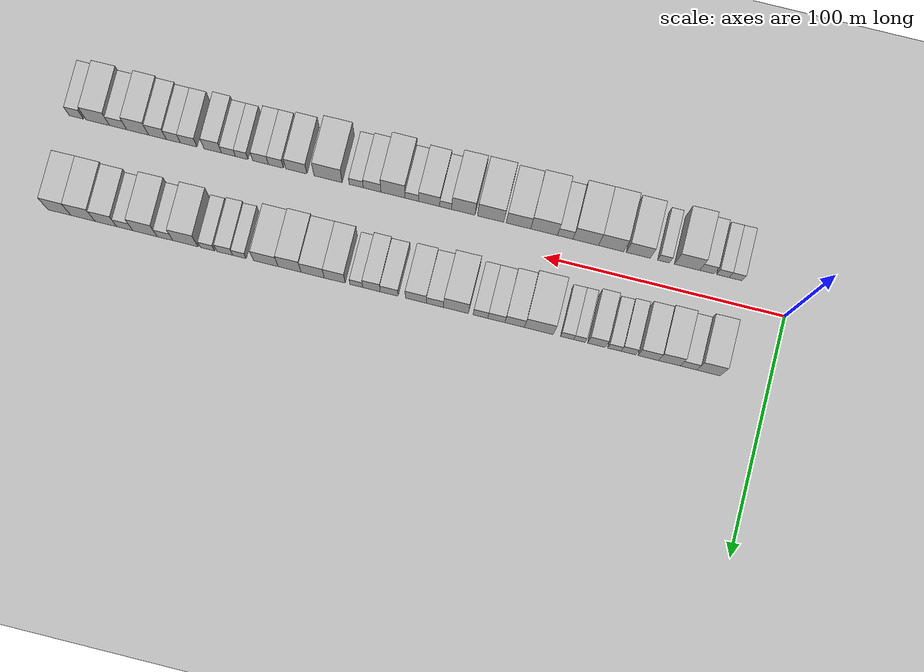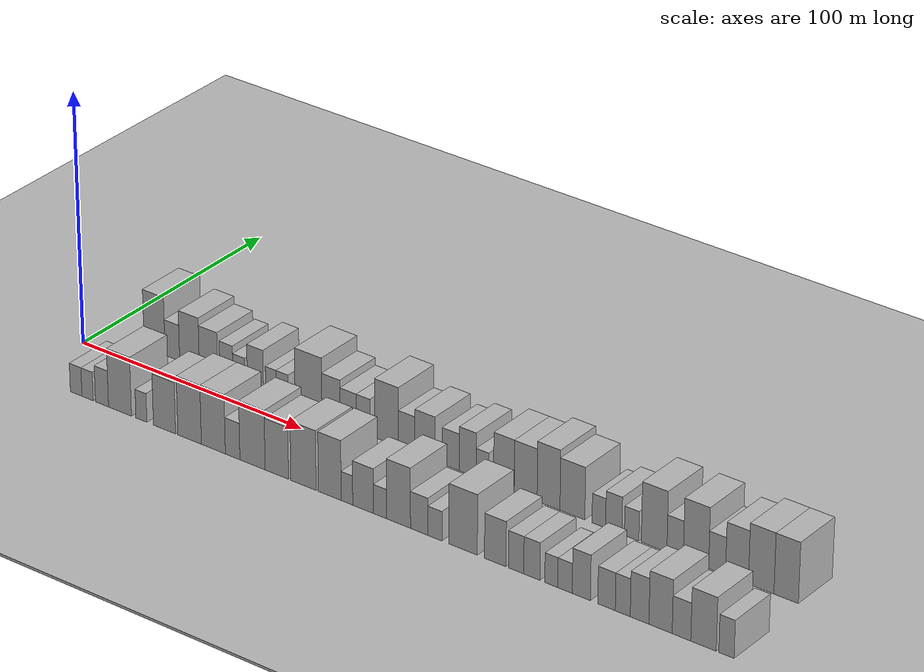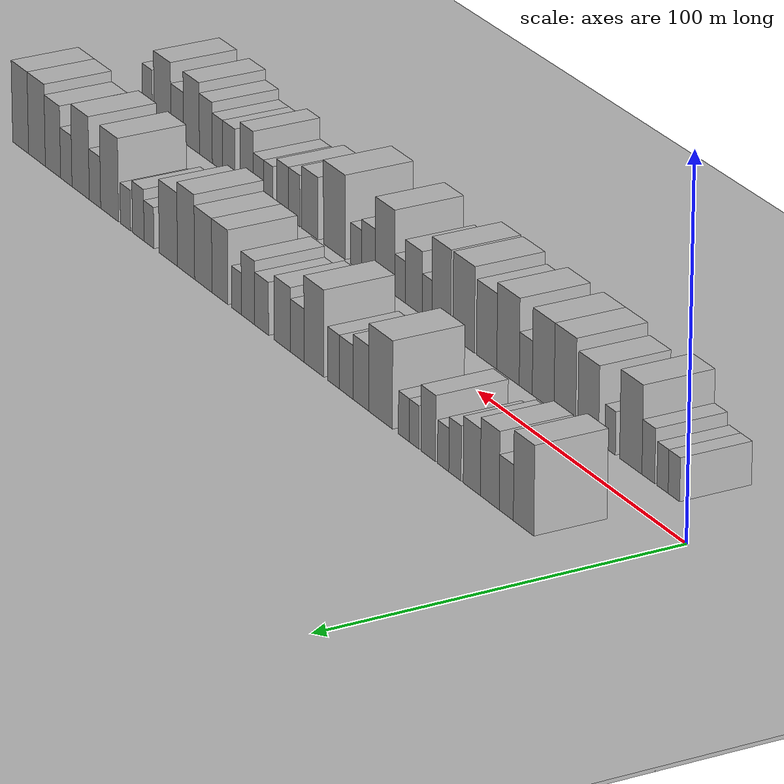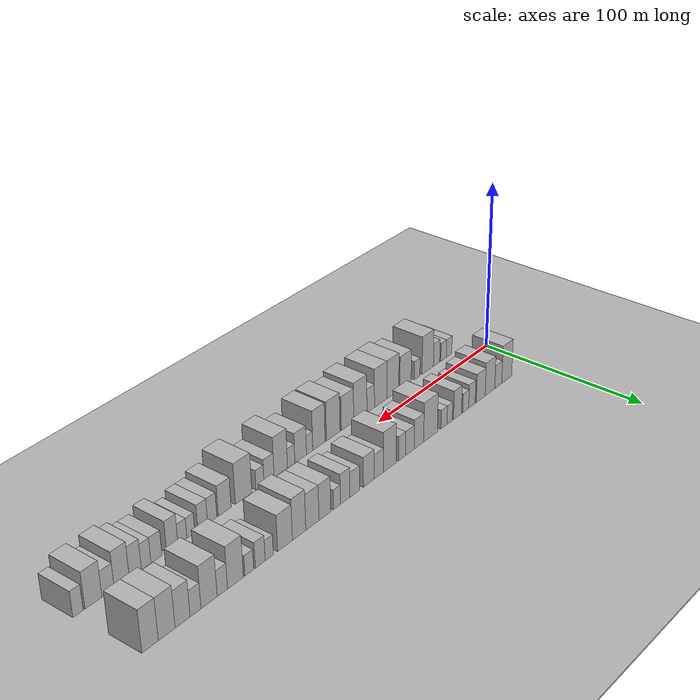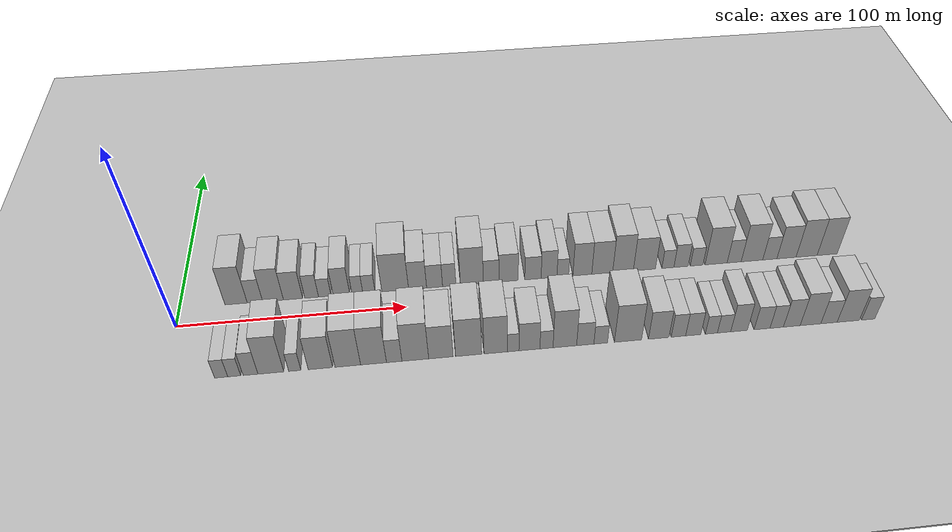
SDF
<?xml version="1.0" encoding="utf-8"?>

<sdf version="1.6">

   <world name="default">

      <gui fullscreen="0">

         <camera name="user_camera">

            <pose>-15 0 4.57585 0 0 0</pose>

            <view_controller>orbit</view_controller>

         </camera>

      </gui>

      <scene>

         <sky>

           <clouds>

             <speed>12</speed>

           </clouds>

         </sky>

         <ambient>0.4 0.4 0.4 1</ambient>

         <background>0.7 0.7 0.7 1</background>

         <shadows>1</shadows>

      </scene>

      <gravity>0 0 -9.8066</gravity>

      <magnetic_field>6e-06 2.3e-05 -4.2e-05</magnetic_field>

      <physics default="0" name="default_physics" type="ode">

         <ode>

            <solver>

               <type>quick</type>

               <iters>10</iters>

               <sor>1.0</sor>

               <use_dynamic_moi_rescaling>0</use_dynamic_moi_rescaling>

            </solver>

            <constraints>

               <cfm>0</cfm>

               <erp>0.2</erp>

               <contact_max_correcting_vel>100</contact_max_correcting_vel>

               <contact_surface_layer>0.001</contact_surface_layer>

            </constraints>

         </ode>

         <max_step_size>0.004</max_step_size>

         <real_time_factor>1</real_time_factor>

         <real_time_update_rate>250</real_time_update_rate>

      </physics>

      <light name="sun" type="directional">

         <cast_shadows>1</cast_shadows>

         <pose>0 0 10 0 0 0</pose>

         <diffuse>0.8 0.8 0.8 1</diffuse>

         <specular>0.2 0.2 0.2 1</specular>

         <attenuation>

            <range>1000</range>

            <constant>0.9</constant>

            <linear>0.01</linear>

            <quadratic>0.001</quadratic>

         </attenuation>

         <direction>-0.5 0.1 -0.9</direction>

      </light>

      <include>

         <name>ground_plane_1</name>

         <uri>model://HANNAS_ground_plane</uri>

         <pose>0 0 0  0 0 0</pose>

      </include>

      <include>

         <name>ground_plane_2</name>

         <uri>model://HANNAS_ground_plane</uri>

         <pose>100 0 0  0 0 0</pose>

      </include>

      <model name="building_1">

         <static>1</static>

         <pose frame="">24.8672 20.0000 0 0.000000 0.000000 1.570796</pose>

         <link name="link">

            <pose frame="">0 0 12.00 0 0 0</pose>

            <collision name="collision">

               <geometry>

                  <box>

                     <size>20.0000 9.7345 24.0000</size>

                  </box>

               </geometry>

               <max_contacts>10</max_contacts>

               <surface>

                  <contact>

                     <ode/>

                  </contact>

                  <bounce/>

                  <friction>

                     <torsional>

                        <ode/>

                     </torsional>

                     <ode/>

                  </friction>

               </surface>

            </collision>

            <visual name="visual">

               <cast_shadows>0</cast_shadows>

               <geometry>

                  <box>

                     <size>20.0000 9.7345 24.0000</size>

                  </box>

               </geometry>

               <material>

                  <script>

                     <uri>model://HANNAS_wall/materials/scripts</uri>

                     <uri>model://HANNAS_wall/materials/textures</uri>

                     <name>vrc/HANNAS_wall</name>

                  </script>

               </material>

            </visual>

            <self_collide>0</self_collide>

            <enable_wind>0</enable_wind>

            <kinematic>0</kinematic>

         </link>

      </model>

      <model name="building_2">

         <static>1</static>

         <pose frame="">33.1002 20.0000 0 0.000000 0.000000 1.570796</pose>

         <link name="link">

            <pose frame="">0 0 7.50 0 0 0</pose>

            <collision name="collision">

               <geometry>

                  <box>

                     <size>20.0000 6.7314 15.0000</size>

                  </box>

               </geometry>

               <max_contacts>10</max_contacts>

               <surface>

                  <contact>

                     <ode/>

                  </contact>

                  <bounce/>

                  <friction>

                     <torsional>

                        <ode/>

                     </torsional>

                     <ode/>

                  </friction>

               </surface>

            </collision>

            <visual name="visual">

               <cast_shadows>0</cast_shadows>

               <geometry>

                  <box>

                     <size>20.0000 6.7314 15.0000</size>

                  </box>

               </geometry>

               <material>

                  <script>

                     <uri>model://HANNAS_wall/materials/scripts</uri>

                     <uri>model://HANNAS_wall/materials/textures</uri>

                     <name>vrc/HANNAS_wall</name>

                  </script>

               </material>

            </visual>

            <self_collide>0</self_collide>

            <enable_wind>0</enable_wind>

            <kinematic>0</kinematic>

         </link>

      </model>

      <model name="building_3">

         <static>1</static>

         <pose frame="">41.0249 20.0000 0 0.000000 0.000000 1.570796</pose>

         <link name="link">

            <pose frame="">0 0 10.50 0 0 0</pose>

            <collision name="collision">

               <geometry>

                  <box>

                     <size>20.0000 9.1180 21.0000</size>

                  </box>

               </geometry>

               <max_contacts>10</max_contacts>

               <surface>

                  <contact>

                     <ode/>

                  </contact>

                  <bounce/>

                  <friction>

                     <torsional>

                        <ode/>

                     </torsional>

                     <ode/>

                  </friction>

               </surface>

            </collision>

            <visual name="visual">

               <cast_shadows>0</cast_shadows>

               <geometry>

                  <box>

                     <size>20.0000 9.1180 21.0000</size>

                  </box>

               </geometry>

               <material>

                  <script>

                     <uri>model://HANNAS_wall/materials/scripts</uri>

                     <uri>model://HANNAS_wall/materials/textures</uri>

                     <name>vrc/HANNAS_wall</name>

                  </script>

               </material>

            </visual>

            <self_collide>0</self_collide>

            <enable_wind>0</enable_wind>

            <kinematic>0</kinematic>

         </link>

      </model>

      <model name="building_4">

         <static>1</static>

         <pose frame="">49.7908 20.0000 0 0.000000 0.000000 1.570796</pose>

         <link name="link">

            <pose frame="">0 0 9.00 0 0 0</pose>

            <collision name="collision">

               <geometry>

                  <box>

                     <size>20.0000 8.4137 18.0000</size>

                  </box>

               </geometry>

               <max_contacts>10</max_contacts>

               <surface>

                  <contact>

                     <ode/>

                  </contact>

                  <bounce/>

                  <friction>

                     <torsional>

                        <ode/>

                     </torsional>

                     <ode/>

                  </friction>

               </surface>

            </collision>

            <visual name="visual">

               <cast_shadows>0</cast_shadows>

               <geometry>

                  <box>

                     <size>20.0000 8.4137 18.0000</size>

                  </box>

               </geometry>

               <material>

                  <script>

                     <uri>model://HANNAS_wall/materials/scripts</uri>

                     <uri>model://HANNAS_wall/materials/textures</uri>

                     <name>vrc/HANNAS_wall</name>

                  </script>

               </material>

            </visual>

            <self_collide>0</self_collide>

            <enable_wind>0</enable_wind>

            <kinematic>0</kinematic>

         </link>

      </model>

      <model name="building_5">

         <static>1</static>

         <pose frame="">58.0168 20.0000 0 0.000000 0.000000 1.570796</pose>

         <link name="link">

            <pose frame="">0 0 7.50 0 0 0</pose>

            <collision name="collision">

               <geometry>

                  <box>

                     <size>20.0000 6.0384 15.0000</size>

                  </box>

               </geometry>

               <max_contacts>10</max_contacts>

               <surface>

                  <contact>

                     <ode/>

                  </contact>

                  <bounce/>

                  <friction>

                     <torsional>

                        <ode/>

                     </torsional>

                     <ode/>

                  </friction>

               </surface>

            </collision>

            <visual name="visual">

               <cast_shadows>0</cast_shadows>

               <geometry>

                  <box>

                     <size>20.0000 6.0384 15.0000</size>

                  </box>

               </geometry>

               <material>

                  <script>

                     <uri>model://HANNAS_wall/materials/scripts</uri>

                     <uri>model://HANNAS_wall/materials/textures</uri>

                     <name>vrc/HANNAS_wall</name>

                  </script>

               </material>

            </visual>

            <self_collide>0</self_collide>

            <enable_wind>0</enable_wind>

            <kinematic>0</kinematic>

         </link>

      </model>

      <model name="building_6">

         <static>1</static>

         <pose frame="">63.8101 20.0000 0 0.000000 0.000000 1.570796</pose>

         <link name="link">

            <pose frame="">0 0 6.00 0 0 0</pose>

            <collision name="collision">

               <geometry>

                  <box>

                     <size>20.0000 5.5482 12.0000</size>

                  </box>

               </geometry>

               <max_contacts>10</max_contacts>

               <surface>

                  <contact>

                     <ode/>

                  </contact>

                  <bounce/>

                  <friction>

                     <torsional>

                        <ode/>

                     </torsional>

                     <ode/>

                  </friction>

               </surface>

            </collision>

            <visual name="visual">

               <cast_shadows>0</cast_shadows>

               <geometry>

                  <box>

                     <size>20.0000 5.5482 12.0000</size>

                  </box>

               </geometry>

               <material>

                  <script>

                     <uri>model://HANNAS_wall/materials/scripts</uri>

                     <uri>model://HANNAS_wall/materials/textures</uri>

                     <name>vrc/HANNAS_wall</name>

                  </script>

               </material>

            </visual>

            <self_collide>0</self_collide>

            <enable_wind>0</enable_wind>

            <kinematic>0</kinematic>

         </link>

      </model>

      <model name="building_7">

         <static>1</static>

         <pose frame="">71.2310 20.0000 0 0.000000 0.000000 1.570796</pose>

         <link name="link">

            <pose frame="">0 0 9.00 0 0 0</pose>

            <collision name="collision">

               <geometry>

                  <box>

                     <size>20.0000 7.2935 18.0000</size>

                  </box>

               </geometry>

               <max_contacts>10</max_contacts>

               <surface>

                  <contact>

                     <ode/>

                  </contact>

                  <bounce/>

                  <friction>

                     <torsional>

                        <ode/>

                     </torsional>

                     <ode/>

                  </friction>

               </surface>

            </collision>

            <visual name="visual">

               <cast_shadows>0</cast_shadows>

               <geometry>

                  <box>

                     <size>20.0000 7.2935 18.0000</size>

                  </box>

               </geometry>

               <material>

                  <script>

                     <uri>model://HANNAS_wall/materials/scripts</uri>

                     <uri>model://HANNAS_wall/materials/textures</uri>

                     <name>vrc/HANNAS_wall</name>

                  </script>

               </material>

            </visual>

            <self_collide>0</self_collide>

            <enable_wind>0</enable_wind>

            <kinematic>0</kinematic>

         </link>

      </model>

      <model name="building_8">

         <static>1</static>

         <pose frame="">78.2869 20.0000 0 0.000000 0.000000 1.570796</pose>

         <link name="link">

            <pose frame="">0 0 6.00 0 0 0</pose>

            <collision name="collision">

               <geometry>

                  <box>

                     <size>20.0000 4.8183 12.0000</size>

                  </box>

               </geometry>

               <max_contacts>10</max_contacts>

               <surface>

                  <contact>

                     <ode/>

                  </contact>

                  <bounce/>

                  <friction>

                     <torsional>

                        <ode/>

                     </torsional>

                     <ode/>

                  </friction>

               </surface>

            </collision>

            <visual name="visual">

               <cast_shadows>0</cast_shadows>

               <geometry>

                  <box>

                     <size>20.0000 4.8183 12.0000</size>

                  </box>

               </geometry>

               <material>

                  <script>

                     <uri>model://HANNAS_wall/materials/scripts</uri>

                     <uri>model://HANNAS_wall/materials/textures</uri>

                     <name>vrc/HANNAS_wall</name>

                  </script>

               </material>

            </visual>

            <self_collide>0</self_collide>

            <enable_wind>0</enable_wind>

            <kinematic>0</kinematic>

         </link>

      </model>

      <model name="building_9">

         <static>1</static>

         <pose frame="">83.4222 20.0000 0 0.000000 0.000000 1.570796</pose>

         <link name="link">

            <pose frame="">0 0 6.00 0 0 0</pose>

            <collision name="collision">

               <geometry>

                  <box>

                     <size>20.0000 5.4523 12.0000</size>

                  </box>

               </geometry>

               <max_contacts>10</max_contacts>

               <surface>

                  <contact>

                     <ode/>

                  </contact>

                  <bounce/>

                  <friction>

                     <torsional>

                        <ode/>

                     </torsional>

                     <ode/>

                  </friction>

               </surface>

            </collision>

            <visual name="visual">

               <cast_shadows>0</cast_shadows>

               <geometry>

                  <box>

                     <size>20.0000 5.4523 12.0000</size>

                  </box>

               </geometry>

               <material>

                  <script>

                     <uri>model://HANNAS_wall/materials/scripts</uri>

                     <uri>model://HANNAS_wall/materials/textures</uri>

                     <name>vrc/HANNAS_wall</name>

                  </script>

               </material>

            </visual>

            <self_collide>0</self_collide>

            <enable_wind>0</enable_wind>

            <kinematic>0</kinematic>

         </link>

      </model>

      <model name="building_10">

         <static>1</static>

         <pose frame="">95.1413 20.0000 0 0.000000 0.000000 1.570796</pose>

         <link name="link">

            <pose frame="">0 0 12.00 0 0 0</pose>

            <collision name="collision">

               <geometry>

                  <box>

                     <size>20.0000 11.9859 24.0000</size>

                  </box>

               </geometry>

               <max_contacts>10</max_contacts>

               <surface>

                  <contact>

                     <ode/>

                  </contact>

                  <bounce/>

                  <friction>

                     <torsional>

                        <ode/>

                     </torsional>

                     <ode/>

                  </friction>

               </surface>

            </collision>

            <visual name="visual">

               <cast_shadows>0</cast_shadows>

               <geometry>

                  <box>

                     <size>20.0000 11.9859 24.0000</size>

                  </box>

               </geometry>

               <material>

                  <script>

                     <uri>model://HANNAS_wall/materials/scripts</uri>

                     <uri>model://HANNAS_wall/materials/textures</uri>

                     <name>vrc/HANNAS_wall</name>

                  </script>

               </material>

            </visual>

            <self_collide>0</self_collide>

            <enable_wind>0</enable_wind>

            <kinematic>0</kinematic>

         </link>

      </model>

      <model name="building_11">

         <static>1</static>

         <pose frame="">105.1921 20.0000 0 0.000000 0.000000 1.570796</pose>

         <link name="link">

            <pose frame="">0 0 9.00 0 0 0</pose>

            <collision name="collision">

               <geometry>

                  <box>

                     <size>20.0000 8.1156 18.0000</size>

                  </box>

               </geometry>

               <max_contacts>10</max_contacts>

               <surface>

                  <contact>

                     <ode/>

                  </contact>

                  <bounce/>

                  <friction>

                     <torsional>

                        <ode/>

                     </torsional>

                     <ode/>

                  </friction>

               </surface>

            </collision>

            <visual name="visual">

               <cast_shadows>0</cast_shadows>

               <geometry>

                  <box>

                     <size>20.0000 8.1156 18.0000</size>

                  </box>

               </geometry>

               <material>

                  <script>

                     <uri>model://HANNAS_wall/materials/scripts</uri>

                     <uri>model://HANNAS_wall/materials/textures</uri>

                     <name>vrc/HANNAS_wall</name>

                  </script>

               </material>

            </visual>

            <self_collide>0</self_collide>

            <enable_wind>0</enable_wind>

            <kinematic>0</kinematic>

         </link>

      </model>

      <model name="building_12">

         <static>1</static>

         <pose frame="">112.8450 20.0000 0 0.000000 0.000000 1.570796</pose>

         <link name="link">

            <pose frame="">0 0 7.50 0 0 0</pose>

            <collision name="collision">

               <geometry>

                  <box>

                     <size>20.0000 7.1903 15.0000</size>

                  </box>

               </geometry>

               <max_contacts>10</max_contacts>

               <surface>

                  <contact>

                     <ode/>

                  </contact>

                  <bounce/>

                  <friction>

                     <torsional>

                        <ode/>

                     </torsional>

                     <ode/>

                  </friction>

               </surface>

            </collision>

            <visual name="visual">

               <cast_shadows>0</cast_shadows>

               <geometry>

                  <box>

                     <size>20.0000 7.1903 15.0000</size>

                  </box>

               </geometry>

               <material>

                  <script>

                     <uri>model://HANNAS_wall/materials/scripts</uri>

                     <uri>model://HANNAS_wall/materials/textures</uri>

                     <name>vrc/HANNAS_wall</name>

                  </script>

               </material>

            </visual>

            <self_collide>0</self_collide>

            <enable_wind>0</enable_wind>

            <kinematic>0</kinematic>

         </link>

      </model>

      <model name="building_13">

         <static>1</static>

         <pose frame="">119.4587 20.0000 0 0.000000 0.000000 1.570796</pose>

         <link name="link">

            <pose frame="">0 0 7.50 0 0 0</pose>

            <collision name="collision">

               <geometry>

                  <box>

                     <size>20.0000 6.0371 15.0000</size>

                  </box>

               </geometry>

               <max_contacts>10</max_contacts>

               <surface>

                  <contact>

                     <ode/>

                  </contact>

                  <bounce/>

                  <friction>

                     <torsional>

                        <ode/>

                     </torsional>

                     <ode/>

                  </friction>

               </surface>

            </collision>

            <visual name="visual">

               <cast_shadows>0</cast_shadows>

               <geometry>

                  <box>

                     <size>20.0000 6.0371 15.0000</size>

                  </box>

               </geometry>

               <material>

                  <script>

                     <uri>model://HANNAS_wall/materials/scripts</uri>

                     <uri>model://HANNAS_wall/materials/textures</uri>

                     <name>vrc/HANNAS_wall</name>

                  </script>

               </material>

            </visual>

            <self_collide>0</self_collide>

            <enable_wind>0</enable_wind>

            <kinematic>0</kinematic>

         </link>

      </model>

      <model name="building_14">

         <static>1</static>

         <pose frame="">129.6978 20.0000 0 0.000000 0.000000 1.570796</pose>

         <link name="link">

            <pose frame="">0 0 12.00 0 0 0</pose>

            <collision name="collision">

               <geometry>

                  <box>

                     <size>20.0000 10.4410 24.0000</size>

                  </box>

               </geometry>

               <max_contacts>10</max_contacts>

               <surface>

                  <contact>

                     <ode/>

                  </contact>

                  <bounce/>

                  <friction>

                     <torsional>

                        <ode/>

                     </torsional>

                     <ode/>

                  </friction>

               </surface>

            </collision>

            <visual name="visual">

               <cast_shadows>0</cast_shadows>

               <geometry>

                  <box>

                     <size>20.0000 10.4410 24.0000</size>

                  </box>

               </geometry>

               <material>

                  <script>

                     <uri>model://HANNAS_wall/materials/scripts</uri>

                     <uri>model://HANNAS_wall/materials/textures</uri>

                     <name>vrc/HANNAS_wall</name>

                  </script>

               </material>

            </visual>

            <self_collide>0</self_collide>

            <enable_wind>0</enable_wind>

            <kinematic>0</kinematic>

         </link>

      </model>

      <model name="building_15">

         <static>1</static>

         <pose frame="">138.4911 20.0000 0 0.000000 0.000000 1.570796</pose>

         <link name="link">

            <pose frame="">0 0 7.50 0 0 0</pose>

            <collision name="collision">

               <geometry>

                  <box>

                     <size>20.0000 7.1457 15.0000</size>

                  </box>

               </geometry>

               <max_contacts>10</max_contacts>

               <surface>

                  <contact>

                     <ode/>

                  </contact>

                  <bounce/>

                  <friction>

                     <torsional>

                        <ode/>

                     </torsional>

                     <ode/>

                  </friction>

               </surface>

            </collision>

            <visual name="visual">

               <cast_shadows>0</cast_shadows>

               <geometry>

                  <box>

                     <size>20.0000 7.1457 15.0000</size>

                  </box>

               </geometry>

               <material>

                  <script>

                     <uri>model://HANNAS_wall/materials/scripts</uri>

                     <uri>model://HANNAS_wall/materials/textures</uri>

                     <name>vrc/HANNAS_wall</name>

                  </script>

               </material>

            </visual>

            <self_collide>0</self_collide>

            <enable_wind>0</enable_wind>

            <kinematic>0</kinematic>

         </link>

      </model>

      <model name="building_16">

         <static>1</static>

         <pose frame="">146.4306 20.0000 0 0.000000 0.000000 1.570796</pose>

         <link name="link">

            <pose frame="">0 0 9.00 0 0 0</pose>

            <collision name="collision">

               <geometry>

                  <box>

                     <size>20.0000 8.7334 18.0000</size>

                  </box>

               </geometry>

               <max_contacts>10</max_contacts>

               <surface>

                  <contact>

                     <ode/>

                  </contact>

                  <bounce/>

                  <friction>

                     <torsional>

                        <ode/>

                     </torsional>

                     <ode/>

                  </friction>

               </surface>

            </collision>

            <visual name="visual">

               <cast_shadows>0</cast_shadows>

               <geometry>

                  <box>

                     <size>20.0000 8.7334 18.0000</size>

                  </box>

               </geometry>

               <material>

                  <script>

                     <uri>model://HANNAS_wall/materials/scripts</uri>

                     <uri>model://HANNAS_wall/materials/textures</uri>

                     <name>vrc/HANNAS_wall</name>

                  </script>

               </material>

            </visual>

            <self_collide>0</self_collide>

            <enable_wind>0</enable_wind>

            <kinematic>0</kinematic>

         </link>

      </model>

      <model name="building_17">

         <static>1</static>

         <pose frame="">157.5419 20.0000 0 0.000000 0.000000 1.570796</pose>

         <link name="link">

            <pose frame="">0 0 7.50 0 0 0</pose>

            <collision name="collision">

               <geometry>

                  <box>

                     <size>20.0000 7.4892 15.0000</size>

                  </box>

               </geometry>

               <max_contacts>10</max_contacts>

               <surface>

                  <contact>

                     <ode/>

                  </contact>

                  <bounce/>

                  <friction>

                     <torsional>

                        <ode/>

                     </torsional>

                     <ode/>

                  </friction>

               </surface>

            </collision>

            <visual name="visual">

               <cast_shadows>0</cast_shadows>

               <geometry>

                  <box>

                     <size>20.0000 7.4892 15.0000</size>

                  </box>

               </geometry>

               <material>

                  <script>

                     <uri>model://HANNAS_wall/materials/scripts</uri>

                     <uri>model://HANNAS_wall/materials/textures</uri>

                     <name>vrc/HANNAS_wall</name>

                  </script>

               </material>

            </visual>

            <self_collide>0</self_collide>

            <enable_wind>0</enable_wind>

            <kinematic>0</kinematic>

         </link>

      </model>

      <model name="building_18">

         <static>1</static>

         <pose frame="">164.9100 20.0000 0 0.000000 0.000000 1.570796</pose>

         <link name="link">

            <pose frame="">0 0 9.00 0 0 0</pose>

            <collision name="collision">

               <geometry>

                  <box>

                     <size>20.0000 7.2470 18.0000</size>

                  </box>

               </geometry>

               <max_contacts>10</max_contacts>

               <surface>

                  <contact>

                     <ode/>

                  </contact>

                  <bounce/>

                  <friction>

                     <torsional>

                        <ode/>

                     </torsional>

                     <ode/>

                  </friction>

               </surface>

            </collision>

            <visual name="visual">

               <cast_shadows>0</cast_shadows>

               <geometry>

                  <box>

                     <size>20.0000 7.2470 18.0000</size>

                  </box>

               </geometry>

               <material>

                  <script>

                     <uri>model://HANNAS_wall/materials/scripts</uri>

                     <uri>model://HANNAS_wall/materials/textures</uri>

                     <name>vrc/HANNAS_wall</name>

                  </script>

               </material>

            </visual>

            <self_collide>0</self_collide>

            <enable_wind>0</enable_wind>

            <kinematic>0</kinematic>

         </link>

      </model>

      <model name="building_19">

         <static>1</static>

         <pose frame="">171.2195 20.0000 0 0.000000 0.000000 1.570796</pose>

         <link name="link">

            <pose frame="">0 0 6.00 0 0 0</pose>

            <collision name="collision">

               <geometry>

                  <box>

                     <size>20.0000 5.3720 12.0000</size>

                  </box>

               </geometry>

               <max_contacts>10</max_contacts>

               <surface>

                  <contact>

                     <ode/>

                  </contact>

                  <bounce/>

                  <friction>

                     <torsional>

                        <ode/>

                     </torsional>

                     <ode/>

                  </friction>

               </surface>

            </collision>

            <visual name="visual">

               <cast_shadows>0</cast_shadows>

               <geometry>

                  <box>

                     <size>20.0000 5.3720 12.0000</size>

                  </box>

               </geometry>

               <material>

                  <script>

                     <uri>model://HANNAS_wall/materials/scripts</uri>

                     <uri>model://HANNAS_wall/materials/textures</uri>

                     <name>vrc/HANNAS_wall</name>

                  </script>

               </material>

            </visual>

            <self_collide>0</self_collide>

            <enable_wind>0</enable_wind>

            <kinematic>0</kinematic>

         </link>

      </model>

      <model name="building_20">

         <static>1</static>

         <pose frame="">180.2682 20.0000 0 0.000000 0.000000 1.570796</pose>

         <link name="link">

            <pose frame="">0 0 10.50 0 0 0</pose>

            <collision name="collision">

               <geometry>

                  <box>

                     <size>20.0000 8.7254 21.0000</size>

                  </box>

               </geometry>

               <max_contacts>10</max_contacts>

               <surface>

                  <contact>

                     <ode/>

                  </contact>

                  <bounce/>

                  <friction>

                     <torsional>

                        <ode/>

                     </torsional>

                     <ode/>

                  </friction>

               </surface>

            </collision>

            <visual name="visual">

               <cast_shadows>0</cast_shadows>

               <geometry>

                  <box>

                     <size>20.0000 8.7254 21.0000</size>

                  </box>

               </geometry>

               <material>

                  <script>

                     <uri>model://HANNAS_wall/materials/scripts</uri>

                     <uri>model://HANNAS_wall/materials/textures</uri>

                     <name>vrc/HANNAS_wall</name>

                  </script>

               </material>

            </visual>

            <self_collide>0</self_collide>

            <enable_wind>0</enable_wind>

            <kinematic>0</kinematic>

         </link>

      </model>

      <model name="building_21">

         <static>1</static>

         <pose frame="">189.4746 20.0000 0 0.000000 0.000000 1.570796</pose>

         <link name="link">

            <pose frame="">0 0 10.50 0 0 0</pose>

            <collision name="collision">

               <geometry>

                  <box>

                     <size>20.0000 9.6873 21.0000</size>

                  </box>

               </geometry>

               <max_contacts>10</max_contacts>

               <surface>

                  <contact>

                     <ode/>

                  </contact>

                  <bounce/>

                  <friction>

                     <torsional>

                        <ode/>

                     </torsional>

                     <ode/>

                  </friction>

               </surface>

            </collision>

            <visual name="visual">

               <cast_shadows>0</cast_shadows>

               <geometry>

                  <box>

                     <size>20.0000 9.6873 21.0000</size>

                  </box>

               </geometry>

               <material>

                  <script>

                     <uri>model://HANNAS_wall/materials/scripts</uri>

                     <uri>model://HANNAS_wall/materials/textures</uri>

                     <name>vrc/HANNAS_wall</name>

                  </script>

               </material>

            </visual>

            <self_collide>0</self_collide>

            <enable_wind>0</enable_wind>

            <kinematic>0</kinematic>

         </link>

      </model>

      <model name="building_22">

         <static>1</static>

         <pose frame="">199.1271 20.0000 0 0.000000 0.000000 1.570796</pose>

         <link name="link">

            <pose frame="">0 0 12.00 0 0 0</pose>

            <collision name="collision">

               <geometry>

                  <box>

                     <size>20.0000 9.6176 24.0000</size>

                  </box>

               </geometry>

               <max_contacts>10</max_contacts>

               <surface>

                  <contact>

                     <ode/>

                  </contact>

                  <bounce/>

                  <friction>

                     <torsional>

                        <ode/>

                     </torsional>

                     <ode/>

                  </friction>

               </surface>

            </collision>

            <visual name="visual">

               <cast_shadows>0</cast_shadows>

               <geometry>

                  <box>

                     <size>20.0000 9.6176 24.0000</size>

                  </box>

               </geometry>

               <material>

                  <script>

                     <uri>model://HANNAS_wall/materials/scripts</uri>

                     <uri>model://HANNAS_wall/materials/textures</uri>

                     <name>vrc/HANNAS_wall</name>

                  </script>

               </material>

            </visual>

            <self_collide>0</self_collide>

            <enable_wind>0</enable_wind>

            <kinematic>0</kinematic>

         </link>

      </model>

      <model name="building_23">

         <static>1</static>

         <pose frame="">209.1204 20.0000 0 0.000000 0.000000 1.570796</pose>

         <link name="link">

            <pose frame="">0 0 10.50 0 0 0</pose>

            <collision name="collision">

               <geometry>

                  <box>

                     <size>20.0000 10.3689 21.0000</size>

                  </box>

               </geometry>

               <max_contacts>10</max_contacts>

               <surface>

                  <contact>

                     <ode/>

                  </contact>

                  <bounce/>

                  <friction>

                     <torsional>

                        <ode/>

                     </torsional>

                     <ode/>

                  </friction>

               </surface>

            </collision>

            <visual name="visual">

               <cast_shadows>0</cast_shadows>

               <geometry>

                  <box>

                     <size>20.0000 10.3689 21.0000</size>

                  </box>

               </geometry>

               <material>

                  <script>

                     <uri>model://HANNAS_wall/materials/scripts</uri>

                     <uri>model://HANNAS_wall/materials/textures</uri>

                     <name>vrc/HANNAS_wall</name>

                  </script>

               </material>

            </visual>

            <self_collide>0</self_collide>

            <enable_wind>0</enable_wind>

            <kinematic>0</kinematic>

         </link>

      </model>

      <model name="building_24">

         <static>1</static>

         <pose frame="">220.1237 20.0000 0 0.000000 0.000000 1.570796</pose>

         <link name="link">

            <pose frame="">0 0 6.00 0 0 0</pose>

            <collision name="collision">

               <geometry>

                  <box>

                     <size>20.0000 5.6377 12.0000</size>

                  </box>

               </geometry>

               <max_contacts>10</max_contacts>

               <surface>

                  <contact>

                     <ode/>

                  </contact>

                  <bounce/>

                  <friction>

                     <torsional>

                        <ode/>

                     </torsional>

                     <ode/>

                  </friction>

               </surface>

            </collision>

            <visual name="visual">

               <cast_shadows>0</cast_shadows>

               <geometry>

                  <box>

                     <size>20.0000 5.6377 12.0000</size>

                  </box>

               </geometry>

               <material>

                  <script>

                     <uri>model://HANNAS_wall/materials/scripts</uri>

                     <uri>model://HANNAS_wall/materials/textures</uri>

                     <name>vrc/HANNAS_wall</name>

                  </script>

               </material>

            </visual>

            <self_collide>0</self_collide>

            <enable_wind>0</enable_wind>

            <kinematic>0</kinematic>

         </link>

      </model>

      <model name="building_25">

         <static>1</static>

         <pose frame="">226.2990 20.0000 0 0.000000 0.000000 1.570796</pose>

         <link name="link">

            <pose frame="">0 0 7.50 0 0 0</pose>

            <collision name="collision">

               <geometry>

                  <box>

                     <size>20.0000 6.7131 15.0000</size>

                  </box>

               </geometry>

               <max_contacts>10</max_contacts>

               <surface>

                  <contact>

                     <ode/>

                  </contact>

                  <bounce/>

                  <friction>

                     <torsional>

                        <ode/>

                     </torsional>

                     <ode/>

                  </friction>

               </surface>

            </collision>

            <visual name="visual">

               <cast_shadows>0</cast_shadows>

               <geometry>

                  <box>

                     <size>20.0000 6.7131 15.0000</size>

                  </box>

               </geometry>

               <material>

                  <script>

                     <uri>model://HANNAS_wall/materials/scripts</uri>

                     <uri>model://HANNAS_wall/materials/textures</uri>

                     <name>vrc/HANNAS_wall</name>

                  </script>

               </material>

            </visual>

            <self_collide>0</self_collide>

            <enable_wind>0</enable_wind>

            <kinematic>0</kinematic>

         </link>

      </model>

      <model name="building_26">

         <static>1</static>

         <pose frame="">233.6371 20.0000 0 0.000000 0.000000 1.570796</pose>

         <link name="link">

            <pose frame="">0 0 6.00 0 0 0</pose>

            <collision name="collision">

               <geometry>

                  <box>

                     <size>20.0000 5.9630 12.0000</size>

                  </box>

               </geometry>

               <max_contacts>10</max_contacts>

               <surface>

                  <contact>

                     <ode/>

                  </contact>

                  <bounce/>

                  <friction>

                     <torsional>

                        <ode/>

                     </torsional>

                     <ode/>

                  </friction>

               </surface>

            </collision>

            <visual name="visual">

               <cast_shadows>0</cast_shadows>

               <geometry>

                  <box>

                     <size>20.0000 5.9630 12.0000</size>

                  </box>

               </geometry>

               <material>

                  <script>

                     <uri>model://HANNAS_wall/materials/scripts</uri>

                     <uri>model://HANNAS_wall/materials/textures</uri>

                     <name>vrc/HANNAS_wall</name>

                  </script>

               </material>

            </visual>

            <self_collide>0</self_collide>

            <enable_wind>0</enable_wind>

            <kinematic>0</kinematic>

         </link>

      </model>

      <model name="building_27">

         <static>1</static>

         <pose frame="">242.8581 20.0000 0 0.000000 0.000000 1.570796</pose>

         <link name="link">

            <pose frame="">0 0 12.00 0 0 0</pose>

            <collision name="collision">

               <geometry>

                  <box>

                     <size>20.0000 10.4790 24.0000</size>

                  </box>

               </geometry>

               <max_contacts>10</max_contacts>

               <surface>

                  <contact>

                     <ode/>

                  </contact>

                  <bounce/>

                  <friction>

                     <torsional>

                        <ode/>

                     </torsional>

                     <ode/>

                  </friction>

               </surface>

            </collision>

            <visual name="visual">

               <cast_shadows>0</cast_shadows>

               <geometry>

                  <box>

                     <size>20.0000 10.4790 24.0000</size>

                  </box>

               </geometry>

               <material>

                  <script>

                     <uri>model://HANNAS_wall/materials/scripts</uri>

                     <uri>model://HANNAS_wall/materials/textures</uri>

                     <name>vrc/HANNAS_wall</name>

                  </script>

               </material>

            </visual>

            <self_collide>0</self_collide>

            <enable_wind>0</enable_wind>

            <kinematic>0</kinematic>

         </link>

      </model>

      <model name="building_28">

         <static>1</static>

         <pose frame="">251.4309 20.0000 0 0.000000 0.000000 1.570796</pose>

         <link name="link">

            <pose frame="">0 0 7.50 0 0 0</pose>

            <collision name="collision">

               <geometry>

                  <box>

                     <size>20.0000 6.6667 15.0000</size>

                  </box>

               </geometry>

               <max_contacts>10</max_contacts>

               <surface>

                  <contact>

                     <ode/>

                  </contact>

                  <bounce/>

                  <friction>

                     <torsional>

                        <ode/>

                     </torsional>

                     <ode/>

                  </friction>

               </surface>

            </collision>

            <visual name="visual">

               <cast_shadows>0</cast_shadows>

               <geometry>

                  <box>

                     <size>20.0000 6.6667 15.0000</size>

                  </box>

               </geometry>

               <material>

                  <script>

                     <uri>model://HANNAS_wall/materials/scripts</uri>

                     <uri>model://HANNAS_wall/materials/textures</uri>

                     <name>vrc/HANNAS_wall</name>

                  </script>

               </material>

            </visual>

            <self_collide>0</self_collide>

            <enable_wind>0</enable_wind>

            <kinematic>0</kinematic>

         </link>

      </model>

      <model name="building_29">

         <static>1</static>

         <pose frame="">259.8941 20.0000 0 0.000000 0.000000 1.570796</pose>

         <link name="link">

            <pose frame="">0 0 12.00 0 0 0</pose>

            <collision name="collision">

               <geometry>

                  <box>

                     <size>20.0000 10.2597 24.0000</size>

                  </box>

               </geometry>

               <max_contacts>10</max_contacts>

               <surface>

                  <contact>

                     <ode/>

                  </contact>

                  <bounce/>

                  <friction>

                     <torsional>

                        <ode/>

                     </torsional>

                     <ode/>

                  </friction>

               </surface>

            </collision>

            <visual name="visual">

               <cast_shadows>0</cast_shadows>

               <geometry>

                  <box>

                     <size>20.0000 10.2597 24.0000</size>

                  </box>

               </geometry>

               <material>

                  <script>

                     <uri>model://HANNAS_wall/materials/scripts</uri>

                     <uri>model://HANNAS_wall/materials/textures</uri>

                     <name>vrc/HANNAS_wall</name>

                  </script>

               </material>

            </visual>

            <self_collide>0</self_collide>

            <enable_wind>0</enable_wind>

            <kinematic>0</kinematic>

         </link>

      </model>

      <model name="building_30">

         <static>1</static>

         <pose frame="">268.4107 20.0000 0 0.000000 0.000000 1.570796</pose>

         <link name="link">

            <pose frame="">0 0 7.50 0 0 0</pose>

            <collision name="collision">

               <geometry>

                  <box>

                     <size>20.0000 6.7736 15.0000</size>

                  </box>

               </geometry>

               <max_contacts>10</max_contacts>

               <surface>

                  <contact>

                     <ode/>

                  </contact>

                  <bounce/>

                  <friction>

                     <torsional>

                        <ode/>

                     </torsional>

                     <ode/>

                  </friction>

               </surface>

            </collision>

            <visual name="visual">

               <cast_shadows>0</cast_shadows>

               <geometry>

                  <box>

                     <size>20.0000 6.7736 15.0000</size>

                  </box>

               </geometry>

               <material>

                  <script>

                     <uri>model://HANNAS_wall/materials/scripts</uri>

                     <uri>model://HANNAS_wall/materials/textures</uri>

                     <name>vrc/HANNAS_wall</name>

                  </script>

               </material>

            </visual>

            <self_collide>0</self_collide>

            <enable_wind>0</enable_wind>

            <kinematic>0</kinematic>

         </link>

      </model>

      <model name="building_31">

         <static>1</static>

         <pose frame="">276.3844 20.0000 0 0.000000 0.000000 1.570796</pose>

         <link name="link">

            <pose frame="">0 0 10.50 0 0 0</pose>

            <collision name="collision">

               <geometry>

                  <box>

                     <size>20.0000 9.1739 21.0000</size>

                  </box>

               </geometry>

               <max_contacts>10</max_contacts>

               <surface>

                  <contact>

                     <ode/>

                  </contact>

                  <bounce/>

                  <friction>

                     <torsional>

                        <ode/>

                     </torsional>

                     <ode/>

                  </friction>

               </surface>

            </collision>

            <visual name="visual">

               <cast_shadows>0</cast_shadows>

               <geometry>

                  <box>

                     <size>20.0000 9.1739 21.0000</size>

                  </box>

               </geometry>

               <material>

                  <script>

                     <uri>model://HANNAS_wall/materials/scripts</uri>

                     <uri>model://HANNAS_wall/materials/textures</uri>

                     <name>vrc/HANNAS_wall</name>

                  </script>

               </material>

            </visual>

            <self_collide>0</self_collide>

            <enable_wind>0</enable_wind>

            <kinematic>0</kinematic>

         </link>

      </model>

      <model name="building_32">

         <static>1</static>

         <pose frame="">286.0506 20.0000 0 0.000000 0.000000 1.570796</pose>

         <link name="link">

            <pose frame="">0 0 12.00 0 0 0</pose>

            <collision name="collision">

               <geometry>

                  <box>

                     <size>20.0000 10.1586 24.0000</size>

                  </box>

               </geometry>

               <max_contacts>10</max_contacts>

               <surface>

                  <contact>

                     <ode/>

                  </contact>

                  <bounce/>

                  <friction>

                     <torsional>

                        <ode/>

                     </torsional>

                     <ode/>

                  </friction>

               </surface>

            </collision>

            <visual name="visual">

               <cast_shadows>0</cast_shadows>

               <geometry>

                  <box>

                     <size>20.0000 10.1586 24.0000</size>

                  </box>

               </geometry>

               <material>

                  <script>

                     <uri>model://HANNAS_wall/materials/scripts</uri>

                     <uri>model://HANNAS_wall/materials/textures</uri>

                     <name>vrc/HANNAS_wall</name>

                  </script>

               </material>

            </visual>

            <self_collide>0</self_collide>

            <enable_wind>0</enable_wind>

            <kinematic>0</kinematic>

         </link>

      </model>

      <model name="building_33">

         <static>1</static>

         <pose frame="">295.9766 20.0000 0 0.000000 0.000000 1.570796</pose>

         <link name="link">

            <pose frame="">0 0 12.00 0 0 0</pose>

            <collision name="collision">

               <geometry>

                  <box>

                     <size>20.0000 9.6934 24.0000</size>

                  </box>

               </geometry>

               <max_contacts>10</max_contacts>

               <surface>

                  <contact>

                     <ode/>

                  </contact>

                  <bounce/>

                  <friction>

                     <torsional>

                        <ode/>

                     </torsional>

                     <ode/>

                  </friction>

               </surface>

            </collision>

            <visual name="visual">

               <cast_shadows>0</cast_shadows>

               <geometry>

                  <box>

                     <size>20.0000 9.6934 24.0000</size>

                  </box>

               </geometry>

               <material>

                  <script>

                     <uri>model://HANNAS_wall/materials/scripts</uri>

                     <uri>model://HANNAS_wall/materials/textures</uri>

                     <name>vrc/HANNAS_wall</name>

                  </script>

               </material>

            </visual>

            <self_collide>0</self_collide>

            <enable_wind>0</enable_wind>

            <kinematic>0</kinematic>

         </link>

      </model>

      <model name="building_34">

         <static>1</static>

         <pose frame="">22.6685 -20.0000 0 0.000000 0.000000 1.570796</pose>

         <link name="link">

            <pose frame="">0 0 6.00 0 0 0</pose>

            <collision name="collision">

               <geometry>

                  <box>

                     <size>20.0000 5.3369 12.0000</size>

                  </box>

               </geometry>

               <max_contacts>10</max_contacts>

               <surface>

                  <contact>

                     <ode/>

                  </contact>

                  <bounce/>

                  <friction>

                     <torsional>

                        <ode/>

                     </torsional>

                     <ode/>

                  </friction>

               </surface>

            </collision>

            <visual name="visual">

               <cast_shadows>0</cast_shadows>

               <geometry>

                  <box>

                     <size>20.0000 5.3369 12.0000</size>

                  </box>

               </geometry>

               <material>

                  <script>

                     <uri>model://HANNAS_wall/materials/scripts</uri>

                     <uri>model://HANNAS_wall/materials/textures</uri>

                     <name>vrc/HANNAS_wall</name>

                  </script>

               </material>

            </visual>

            <self_collide>0</self_collide>

            <enable_wind>0</enable_wind>

            <kinematic>0</kinematic>

         </link>

      </model>

      <model name="building_35">

         <static>1</static>

         <pose frame="">27.9637 -20.0000 0 0.000000 0.000000 1.570796</pose>

         <link name="link">

            <pose frame="">0 0 6.00 0 0 0</pose>

            <collision name="collision">

               <geometry>

                  <box>

                     <size>20.0000 5.2535 12.0000</size>

                  </box>

               </geometry>

               <max_contacts>10</max_contacts>

               <surface>

                  <contact>

                     <ode/>

                  </contact>

                  <bounce/>

                  <friction>

                     <torsional>

                        <ode/>

                     </torsional>

                     <ode/>

                  </friction>

               </surface>

            </collision>

            <visual name="visual">

               <cast_shadows>0</cast_shadows>

               <geometry>

                  <box>

                     <size>20.0000 5.2535 12.0000</size>

                  </box>

               </geometry>

               <material>

                  <script>

                     <uri>model://HANNAS_wall/materials/scripts</uri>

                     <uri>model://HANNAS_wall/materials/textures</uri>

                     <name>vrc/HANNAS_wall</name>

                  </script>

               </material>

            </visual>

            <self_collide>0</self_collide>

            <enable_wind>0</enable_wind>

            <kinematic>0</kinematic>

         </link>

      </model>

      <model name="building_36">

         <static>1</static>

         <pose frame="">34.6058 -20.0000 0 0.000000 0.000000 1.570796</pose>

         <link name="link">

            <pose frame="">0 0 7.50 0 0 0</pose>

            <collision name="collision">

               <geometry>

                  <box>

                     <size>20.0000 6.0309 15.0000</size>

                  </box>

               </geometry>

               <max_contacts>10</max_contacts>

               <surface>

                  <contact>

                     <ode/>

                  </contact>

                  <bounce/>

                  <friction>

                     <torsional>

                        <ode/>

                     </torsional>

                     <ode/>

                  </friction>

               </surface>

            </collision>

            <visual name="visual">

               <cast_shadows>0</cast_shadows>

               <geometry>

                  <box>

                     <size>20.0000 6.0309 15.0000</size>

                  </box>

               </geometry>

               <material>

                  <script>

                     <uri>model://HANNAS_wall/materials/scripts</uri>

                     <uri>model://HANNAS_wall/materials/textures</uri>

                     <name>vrc/HANNAS_wall</name>

                  </script>

               </material>

            </visual>

            <self_collide>0</self_collide>

            <enable_wind>0</enable_wind>

            <kinematic>0</kinematic>

         </link>

      </model>

      <model name="building_37">

         <static>1</static>

         <pose frame="">42.8942 -20.0000 0 0.000000 0.000000 1.570796</pose>

         <link name="link">

            <pose frame="">0 0 12.00 0 0 0</pose>

            <collision name="collision">

               <geometry>

                  <box>

                     <size>20.0000 10.5458 24.0000</size>

                  </box>

               </geometry>

               <max_contacts>10</max_contacts>

               <surface>

                  <contact>

                     <ode/>

                  </contact>

                  <bounce/>

                  <friction>

                     <torsional>

                        <ode/>

                     </torsional>

                     <ode/>

                  </friction>

               </surface>

            </collision>

            <visual name="visual">

               <cast_shadows>0</cast_shadows>

               <geometry>

                  <box>

                     <size>20.0000 10.5458 24.0000</size>

                  </box>

               </geometry>

               <material>

                  <script>

                     <uri>model://HANNAS_wall/materials/scripts</uri>

                     <uri>model://HANNAS_wall/materials/textures</uri>

                     <name>vrc/HANNAS_wall</name>

                  </script>

               </material>

            </visual>

            <self_collide>0</self_collide>

            <enable_wind>0</enable_wind>

            <kinematic>0</kinematic>

         </link>

      </model>

      <model name="building_38">

         <static>1</static>

         <pose frame="">52.6691 -20.0000 0 0.000000 0.000000 1.570796</pose>

         <link name="link">

            <pose frame="">0 0 6.00 0 0 0</pose>

            <collision name="collision">

               <geometry>

                  <box>

                     <size>20.0000 5.0041 12.0000</size>

                  </box>

               </geometry>

               <max_contacts>10</max_contacts>

               <surface>

                  <contact>

                     <ode/>

                  </contact>

                  <bounce/>

                  <friction>

                     <torsional>

                        <ode/>

                     </torsional>

                     <ode/>

                  </friction>

               </surface>

            </collision>

            <visual name="visual">

               <cast_shadows>0</cast_shadows>

               <geometry>

                  <box>

                     <size>20.0000 5.0041 12.0000</size>

                  </box>

               </geometry>

               <material>

                  <script>

                     <uri>model://HANNAS_wall/materials/scripts</uri>

                     <uri>model://HANNAS_wall/materials/textures</uri>

                     <name>vrc/HANNAS_wall</name>

                  </script>

               </material>

            </visual>

            <self_collide>0</self_collide>

            <enable_wind>0</enable_wind>

            <kinematic>0</kinematic>

         </link>

      </model>

      <model name="building_39">

         <static>1</static>

         <pose frame="">63.1974 -20.0000 0 0.000000 0.000000 1.570796</pose>

         <link name="link">

            <pose frame="">0 0 10.50 0 0 0</pose>

            <collision name="collision">

               <geometry>

                  <box>

                     <size>20.0000 10.0524 21.0000</size>

                  </box>

               </geometry>

               <max_contacts>10</max_contacts>

               <surface>

                  <contact>

                     <ode/>

                  </contact>

                  <bounce/>

                  <friction>

                     <torsional>

                        <ode/>

                     </torsional>

                     <ode/>

                  </friction>

               </surface>

            </collision>

            <visual name="visual">

               <cast_shadows>0</cast_shadows>

               <geometry>

                  <box>

                     <size>20.0000 10.0524 21.0000</size>

                  </box>

               </geometry>

               <material>

                  <script>

                     <uri>model://HANNAS_wall/materials/scripts</uri>

                     <uri>model://HANNAS_wall/materials/textures</uri>

                     <name>vrc/HANNAS_wall</name>

                  </script>

               </material>

            </visual>

            <self_collide>0</self_collide>

            <enable_wind>0</enable_wind>

            <kinematic>0</kinematic>

         </link>

      </model>

      <model name="building_40">

         <static>1</static>

         <pose frame="">74.5161 -20.0000 0 0.000000 0.000000 1.570796</pose>

         <link name="link">

            <pose frame="">0 0 12.00 0 0 0</pose>

            <collision name="collision">

               <geometry>

                  <box>

                     <size>20.0000 10.5849 24.0000</size>

                  </box>

               </geometry>

               <max_contacts>10</max_contacts>

               <surface>

                  <contact>

                     <ode/>

                  </contact>

                  <bounce/>

                  <friction>

                     <torsional>

                        <ode/>

                     </torsional>

                     <ode/>

                  </friction>

               </surface>

            </collision>

            <visual name="visual">

               <cast_shadows>0</cast_shadows>

               <geometry>

                  <box>

                     <size>20.0000 10.5849 24.0000</size>

                  </box>

               </geometry>

               <material>

                  <script>

                     <uri>model://HANNAS_wall/materials/scripts</uri>

                     <uri>model://HANNAS_wall/materials/textures</uri>

                     <name>vrc/HANNAS_wall</name>

                  </script>

               </material>

            </visual>

            <self_collide>0</self_collide>

            <enable_wind>0</enable_wind>

            <kinematic>0</kinematic>

         </link>

      </model>

      <model name="building_41">

         <static>1</static>

         <pose frame="">85.1882 -20.0000 0 0.000000 0.000000 1.570796</pose>

         <link name="link">

            <pose frame="">0 0 12.00 0 0 0</pose>

            <collision name="collision">

               <geometry>

                  <box>

                     <size>20.0000 10.7592 24.0000</size>

                  </box>

               </geometry>

               <max_contacts>10</max_contacts>

               <surface>

                  <contact>

                     <ode/>

                  </contact>

                  <bounce/>

                  <friction>

                     <torsional>

                        <ode/>

                     </torsional>

                     <ode/>

                  </friction>

               </surface>

            </collision>

            <visual name="visual">

               <cast_shadows>0</cast_shadows>

               <geometry>

                  <box>

                     <size>20.0000 10.7592 24.0000</size>

                  </box>

               </geometry>

               <material>

                  <script>

                     <uri>model://HANNAS_wall/materials/scripts</uri>

                     <uri>model://HANNAS_wall/materials/textures</uri>

                     <name>vrc/HANNAS_wall</name>

                  </script>

               </material>

            </visual>

            <self_collide>0</self_collide>

            <enable_wind>0</enable_wind>

            <kinematic>0</kinematic>

         </link>

      </model>

      <model name="building_42">

         <static>1</static>

         <pose frame="">93.7894 -20.0000 0 0.000000 0.000000 1.570796</pose>

         <link name="link">

            <pose frame="">0 0 7.50 0 0 0</pose>

            <collision name="collision">

               <geometry>

                  <box>

                     <size>20.0000 6.4432 15.0000</size>

                  </box>

               </geometry>

               <max_contacts>10</max_contacts>

               <surface>

                  <contact>

                     <ode/>

                  </contact>

                  <bounce/>

                  <friction>

                     <torsional>

                        <ode/>

                     </torsional>

                     <ode/>

                  </friction>

               </surface>

            </collision>

            <visual name="visual">

               <cast_shadows>0</cast_shadows>

               <geometry>

                  <box>

                     <size>20.0000 6.4432 15.0000</size>

                  </box>

               </geometry>

               <material>

                  <script>

                     <uri>model://HANNAS_wall/materials/scripts</uri>

                     <uri>model://HANNAS_wall/materials/textures</uri>

                     <name>vrc/HANNAS_wall</name>

                  </script>

               </material>

            </visual>

            <self_collide>0</self_collide>

            <enable_wind>0</enable_wind>

            <kinematic>0</kinematic>

         </link>

      </model>

      <model name="building_43">

         <static>1</static>

         <pose frame="">102.6106 -20.0000 0 0.000000 0.000000 1.570796</pose>

         <link name="link">

            <pose frame="">0 0 12.00 0 0 0</pose>

            <collision name="collision">

               <geometry>

                  <box>

                     <size>20.0000 11.1993 24.0000</size>

                  </box>

               </geometry>

               <max_contacts>10</max_contacts>

               <surface>

                  <contact>

                     <ode/>

                  </contact>

                  <bounce/>

                  <friction>

                     <torsional>

                        <ode/>

                     </torsional>

                     <ode/>

                  </friction>

               </surface>

            </collision>

            <visual name="visual">

               <cast_shadows>0</cast_shadows>

               <geometry>

                  <box>

                     <size>20.0000 11.1993 24.0000</size>

                  </box>

               </geometry>

               <material>

                  <script>

                     <uri>model://HANNAS_wall/materials/scripts</uri>

                     <uri>model://HANNAS_wall/materials/textures</uri>

                     <name>vrc/HANNAS_wall</name>

                  </script>

               </material>

            </visual>

            <self_collide>0</self_collide>

            <enable_wind>0</enable_wind>

            <kinematic>0</kinematic>

         </link>

      </model>

      <model name="building_44">

         <static>1</static>

         <pose frame="">113.3505 -20.0000 0 0.000000 0.000000 1.570796</pose>

         <link name="link">

            <pose frame="">0 0 10.50 0 0 0</pose>

            <collision name="collision">

               <geometry>

                  <box>

                     <size>20.0000 10.2805 21.0000</size>

                  </box>

               </geometry>

               <max_contacts>10</max_contacts>

               <surface>

                  <contact>

                     <ode/>

                  </contact>

                  <bounce/>

                  <friction>

                     <torsional>

                        <ode/>

                     </torsional>

                     <ode/>

                  </friction>

               </surface>

            </collision>

            <visual name="visual">

               <cast_shadows>0</cast_shadows>

               <geometry>

                  <box>

                     <size>20.0000 10.2805 21.0000</size>

                  </box>

               </geometry>

               <material>

                  <script>

                     <uri>model://HANNAS_wall/materials/scripts</uri>

                     <uri>model://HANNAS_wall/materials/textures</uri>

                     <name>vrc/HANNAS_wall</name>

                  </script>

               </material>

            </visual>

            <self_collide>0</self_collide>

            <enable_wind>0</enable_wind>

            <kinematic>0</kinematic>

         </link>

      </model>

      <model name="building_45">

         <static>1</static>

         <pose frame="">125.0140 -20.0000 0 0.000000 0.000000 1.570796</pose>

         <link name="link">

            <pose frame="">0 0 12.00 0 0 0</pose>

            <collision name="collision">

               <geometry>

                  <box>

                     <size>20.0000 11.0466 24.0000</size>

                  </box>

               </geometry>

               <max_contacts>10</max_contacts>

               <surface>

                  <contact>

                     <ode/>

                  </contact>

                  <bounce/>

                  <friction>

                     <torsional>

                        <ode/>

                     </torsional>

                     <ode/>

                  </friction>

               </surface>

            </collision>

            <visual name="visual">

               <cast_shadows>0</cast_shadows>

               <geometry>

                  <box>

                     <size>20.0000 11.0466 24.0000</size>

                  </box>

               </geometry>

               <material>

                  <script>

                     <uri>model://HANNAS_wall/materials/scripts</uri>

                     <uri>model://HANNAS_wall/materials/textures</uri>

                     <name>vrc/HANNAS_wall</name>

                  </script>

               </material>

            </visual>

            <self_collide>0</self_collide>

            <enable_wind>0</enable_wind>

            <kinematic>0</kinematic>

         </link>

      </model>

      <model name="building_46">

         <static>1</static>

         <pose frame="">136.4713 -20.0000 0 0.000000 0.000000 1.570796</pose>

         <link name="link">

            <pose frame="">0 0 12.00 0 0 0</pose>

            <collision name="collision">

               <geometry>

                  <box>

                     <size>20.0000 9.8679 24.0000</size>

                  </box>

               </geometry>

               <max_contacts>10</max_contacts>

               <surface>

                  <contact>

                     <ode/>

                  </contact>

                  <bounce/>

                  <friction>

                     <torsional>

                        <ode/>

                     </torsional>

                     <ode/>

                  </friction>

               </surface>

            </collision>

            <visual name="visual">

               <cast_shadows>0</cast_shadows>

               <geometry>

                  <box>

                     <size>20.0000 9.8679 24.0000</size>

                  </box>

               </geometry>

               <material>

                  <script>

                     <uri>model://HANNAS_wall/materials/scripts</uri>

                     <uri>model://HANNAS_wall/materials/textures</uri>

                     <name>vrc/HANNAS_wall</name>

                  </script>

               </material>

            </visual>

            <self_collide>0</self_collide>

            <enable_wind>0</enable_wind>

            <kinematic>0</kinematic>

         </link>

      </model>

      <model name="building_47">

         <static>1</static>

         <pose frame="">143.8882 -20.0000 0 0.000000 0.000000 1.570796</pose>

         <link name="link">

            <pose frame="">0 0 6.00 0 0 0</pose>

            <collision name="collision">

               <geometry>

                  <box>

                     <size>20.0000 4.9659 12.0000</size>

                  </box>

               </geometry>

               <max_contacts>10</max_contacts>

               <surface>

                  <contact>

                     <ode/>

                  </contact>

                  <bounce/>

                  <friction>

                     <torsional>

                        <ode/>

                     </torsional>

                     <ode/>

                  </friction>

               </surface>

            </collision>

            <visual name="visual">

               <cast_shadows>0</cast_shadows>

               <geometry>

                  <box>

                     <size>20.0000 4.9659 12.0000</size>

                  </box>

               </geometry>

               <material>

                  <script>

                     <uri>model://HANNAS_wall/materials/scripts</uri>

                     <uri>model://HANNAS_wall/materials/textures</uri>

                     <name>vrc/HANNAS_wall</name>

                  </script>

               </material>

            </visual>

            <self_collide>0</self_collide>

            <enable_wind>0</enable_wind>

            <kinematic>0</kinematic>

         </link>

      </model>

      <model name="building_48">

         <static>1</static>

         <pose frame="">150.8510 -20.0000 0 0.000000 0.000000 1.570796</pose>

         <link name="link">

            <pose frame="">0 0 9.00 0 0 0</pose>

            <collision name="collision">

               <geometry>

                  <box>

                     <size>20.0000 8.9597 18.0000</size>

                  </box>

               </geometry>

               <max_contacts>10</max_contacts>

               <surface>

                  <contact>

                     <ode/>

                  </contact>

                  <bounce/>

                  <friction>

                     <torsional>

                        <ode/>

                     </torsional>

                     <ode/>

                  </friction>

               </surface>

            </collision>

            <visual name="visual">

               <cast_shadows>0</cast_shadows>

               <geometry>

                  <box>

                     <size>20.0000 8.9597 18.0000</size>

                  </box>

               </geometry>

               <material>

                  <script>

                     <uri>model://HANNAS_wall/materials/scripts</uri>

                     <uri>model://HANNAS_wall/materials/textures</uri>

                     <name>vrc/HANNAS_wall</name>

                  </script>

               </material>

            </visual>

            <self_collide>0</self_collide>

            <enable_wind>0</enable_wind>

            <kinematic>0</kinematic>

         </link>

      </model>

      <model name="building_49">

         <static>1</static>

         <pose frame="">158.1245 -20.0000 0 0.000000 0.000000 1.570796</pose>

         <link name="link">

            <pose frame="">0 0 6.00 0 0 0</pose>

            <collision name="collision">

               <geometry>

                  <box>

                     <size>20.0000 5.5873 12.0000</size>

                  </box>

               </geometry>

               <max_contacts>10</max_contacts>

               <surface>

                  <contact>

                     <ode/>

                  </contact>

                  <bounce/>

                  <friction>

                     <torsional>

                        <ode/>

                     </torsional>

                     <ode/>

                  </friction>

               </surface>

            </collision>

            <visual name="visual">

               <cast_shadows>0</cast_shadows>

               <geometry>

                  <box>

                     <size>20.0000 5.5873 12.0000</size>

                  </box>

               </geometry>

               <material>

                  <script>

                     <uri>model://HANNAS_wall/materials/scripts</uri>

                     <uri>model://HANNAS_wall/materials/textures</uri>

                     <name>vrc/HANNAS_wall</name>

                  </script>

               </material>

            </visual>

            <self_collide>0</self_collide>

            <enable_wind>0</enable_wind>

            <kinematic>0</kinematic>

         </link>

      </model>

      <model name="building_50">

         <static>1</static>

         <pose frame="">165.9879 -20.0000 0 0.000000 0.000000 1.570796</pose>

         <link name="link">

            <pose frame="">0 0 12.00 0 0 0</pose>

            <collision name="collision">

               <geometry>

                  <box>

                     <size>20.0000 10.1395 24.0000</size>

                  </box>

               </geometry>

               <max_contacts>10</max_contacts>

               <surface>

                  <contact>

                     <ode/>

                  </contact>

                  <bounce/>

                  <friction>

                     <torsional>

                        <ode/>

                     </torsional>

                     <ode/>

                  </friction>

               </surface>

            </collision>

            <visual name="visual">

               <cast_shadows>0</cast_shadows>

               <geometry>

                  <box>

                     <size>20.0000 10.1395 24.0000</size>

                  </box>

               </geometry>

               <material>

                  <script>

                     <uri>model://HANNAS_wall/materials/scripts</uri>

                     <uri>model://HANNAS_wall/materials/textures</uri>

                     <name>vrc/HANNAS_wall</name>

                  </script>

               </material>

            </visual>

            <self_collide>0</self_collide>

            <enable_wind>0</enable_wind>

            <kinematic>0</kinematic>

         </link>

      </model>

      <model name="building_51">

         <static>1</static>

         <pose frame="">174.7690 -20.0000 0 0.000000 0.000000 1.570796</pose>

         <link name="link">

            <pose frame="">0 0 7.50 0 0 0</pose>

            <collision name="collision">

               <geometry>

                  <box>

                     <size>20.0000 7.4229 15.0000</size>

                  </box>

               </geometry>

               <max_contacts>10</max_contacts>

               <surface>

                  <contact>

                     <ode/>

                  </contact>

                  <bounce/>

                  <friction>

                     <torsional>

                        <ode/>

                     </torsional>

                     <ode/>

                  </friction>

               </surface>

            </collision>

            <visual name="visual">

               <cast_shadows>0</cast_shadows>

               <geometry>

                  <box>

                     <size>20.0000 7.4229 15.0000</size>

                  </box>

               </geometry>

               <material>

                  <script>

                     <uri>model://HANNAS_wall/materials/scripts</uri>

                     <uri>model://HANNAS_wall/materials/textures</uri>

                     <name>vrc/HANNAS_wall</name>

                  </script>

               </material>

            </visual>

            <self_collide>0</self_collide>

            <enable_wind>0</enable_wind>

            <kinematic>0</kinematic>

         </link>

      </model>

      <model name="building_52">

         <static>1</static>

         <pose frame="">181.4271 -20.0000 0 0.000000 0.000000 1.570796</pose>

         <link name="link">

            <pose frame="">0 0 6.00 0 0 0</pose>

            <collision name="collision">

               <geometry>

                  <box>

                     <size>20.0000 5.8933 12.0000</size>

                  </box>

               </geometry>

               <max_contacts>10</max_contacts>

               <surface>

                  <contact>

                     <ode/>

                  </contact>

                  <bounce/>

                  <friction>

                     <torsional>

                        <ode/>

                     </torsional>

                     <ode/>

                  </friction>

               </surface>

            </collision>

            <visual name="visual">

               <cast_shadows>0</cast_shadows>

               <geometry>

                  <box>

                     <size>20.0000 5.8933 12.0000</size>

                  </box>

               </geometry>

               <material>

                  <script>

                     <uri>model://HANNAS_wall/materials/scripts</uri>

                     <uri>model://HANNAS_wall/materials/textures</uri>

                     <name>vrc/HANNAS_wall</name>

                  </script>

               </material>

            </visual>

            <self_collide>0</self_collide>

            <enable_wind>0</enable_wind>

            <kinematic>0</kinematic>

         </link>

      </model>

      <model name="building_53">

         <static>1</static>

         <pose frame="">193.2833 -20.0000 0 0.000000 0.000000 1.570796</pose>

         <link name="link">

            <pose frame="">0 0 12.00 0 0 0</pose>

            <collision name="collision">

               <geometry>

                  <box>

                     <size>20.0000 11.8191 24.0000</size>

                  </box>

               </geometry>

               <max_contacts>10</max_contacts>

               <surface>

                  <contact>

                     <ode/>

                  </contact>

                  <bounce/>

                  <friction>

                     <torsional>

                        <ode/>

                     </torsional>

                     <ode/>

                  </friction>

               </surface>

            </collision>

            <visual name="visual">

               <cast_shadows>0</cast_shadows>

               <geometry>

                  <box>

                     <size>20.0000 11.8191 24.0000</size>

                  </box>

               </geometry>

               <material>

                  <script>

                     <uri>model://HANNAS_wall/materials/scripts</uri>

                     <uri>model://HANNAS_wall/materials/textures</uri>

                     <name>vrc/HANNAS_wall</name>

                  </script>

               </material>

            </visual>

            <self_collide>0</self_collide>

            <enable_wind>0</enable_wind>

            <kinematic>0</kinematic>

         </link>

      </model>

      <model name="building_54">

         <static>1</static>

         <pose frame="">206.6568 -20.0000 0 0.000000 0.000000 1.570796</pose>

         <link name="link">

            <pose frame="">0 0 9.00 0 0 0</pose>

            <collision name="collision">

               <geometry>

                  <box>

                     <size>20.0000 8.9279 18.0000</size>

                  </box>

               </geometry>

               <max_contacts>10</max_contacts>

               <surface>

                  <contact>

                     <ode/>

                  </contact>

                  <bounce/>

                  <friction>

                     <torsional>

                        <ode/>

                     </torsional>

                     <ode/>

                  </friction>

               </surface>

            </collision>

            <visual name="visual">

               <cast_shadows>0</cast_shadows>

               <geometry>

                  <box>

                     <size>20.0000 8.9279 18.0000</size>

                  </box>

               </geometry>

               <material>

                  <script>

                     <uri>model://HANNAS_wall/materials/scripts</uri>

                     <uri>model://HANNAS_wall/materials/textures</uri>

                     <name>vrc/HANNAS_wall</name>

                  </script>

               </material>

            </visual>

            <self_collide>0</self_collide>

            <enable_wind>0</enable_wind>

            <kinematic>0</kinematic>

         </link>

      </model>

      <model name="building_55">

         <static>1</static>

         <pose frame="">215.2826 -20.0000 0 0.000000 0.000000 1.570796</pose>

         <link name="link">

            <pose frame="">0 0 7.50 0 0 0</pose>

            <collision name="collision">

               <geometry>

                  <box>

                     <size>20.0000 6.3238 15.0000</size>

                  </box>

               </geometry>

               <max_contacts>10</max_contacts>

               <surface>

                  <contact>

                     <ode/>

                  </contact>

                  <bounce/>

                  <friction>

                     <torsional>

                        <ode/>

                     </torsional>

                     <ode/>

                  </friction>

               </surface>

            </collision>

            <visual name="visual">

               <cast_shadows>0</cast_shadows>

               <geometry>

                  <box>

                     <size>20.0000 6.3238 15.0000</size>

                  </box>

               </geometry>

               <material>

                  <script>

                     <uri>model://HANNAS_wall/materials/scripts</uri>

                     <uri>model://HANNAS_wall/materials/textures</uri>

                     <name>vrc/HANNAS_wall</name>

                  </script>

               </material>

            </visual>

            <self_collide>0</self_collide>

            <enable_wind>0</enable_wind>

            <kinematic>0</kinematic>

         </link>

      </model>

      <model name="building_56">

         <static>1</static>

         <pose frame="">221.7732 -20.0000 0 0.000000 0.000000 1.570796</pose>

         <link name="link">

            <pose frame="">0 0 7.50 0 0 0</pose>

            <collision name="collision">

               <geometry>

                  <box>

                     <size>20.0000 6.6573 15.0000</size>

                  </box>

               </geometry>

               <max_contacts>10</max_contacts>

               <surface>

                  <contact>

                     <ode/>

                  </contact>

                  <bounce/>

                  <friction>

                     <torsional>

                        <ode/>

                     </torsional>

                     <ode/>

                  </friction>

               </surface>

            </collision>

            <visual name="visual">

               <cast_shadows>0</cast_shadows>

               <geometry>

                  <box>

                     <size>20.0000 6.6573 15.0000</size>

                  </box>

               </geometry>

               <material>

                  <script>

                     <uri>model://HANNAS_wall/materials/scripts</uri>

                     <uri>model://HANNAS_wall/materials/textures</uri>

                     <name>vrc/HANNAS_wall</name>

                  </script>

               </material>

            </visual>

            <self_collide>0</self_collide>

            <enable_wind>0</enable_wind>

            <kinematic>0</kinematic>

         </link>

      </model>

      <model name="building_57">

         <static>1</static>

         <pose frame="">229.7587 -20.0000 0 0.000000 0.000000 1.570796</pose>

         <link name="link">

            <pose frame="">0 0 6.00 0 0 0</pose>

            <collision name="collision">

               <geometry>

                  <box>

                     <size>20.0000 5.3136 12.0000</size>

                  </box>

               </geometry>

               <max_contacts>10</max_contacts>

               <surface>

                  <contact>

                     <ode/>

                  </contact>

                  <bounce/>

                  <friction>

                     <torsional>

                        <ode/>

                     </torsional>

                     <ode/>

                  </friction>

               </surface>

            </collision>

            <visual name="visual">

               <cast_shadows>0</cast_shadows>

               <geometry>

                  <box>

                     <size>20.0000 5.3136 12.0000</size>

                  </box>

               </geometry>

               <material>

                  <script>

                     <uri>model://HANNAS_wall/materials/scripts</uri>

                     <uri>model://HANNAS_wall/materials/textures</uri>

                     <name>vrc/HANNAS_wall</name>

                  </script>

               </material>

            </visual>

            <self_collide>0</self_collide>

            <enable_wind>0</enable_wind>

            <kinematic>0</kinematic>

         </link>

      </model>

      <model name="building_58">

         <static>1</static>

         <pose frame="">235.3488 -20.0000 0 0.000000 0.000000 1.570796</pose>

         <link name="link">

            <pose frame="">0 0 6.00 0 0 0</pose>

            <collision name="collision">

               <geometry>

                  <box>

                     <size>20.0000 5.8667 12.0000</size>

                  </box>

               </geometry>

               <max_contacts>10</max_contacts>

               <surface>

                  <contact>

                     <ode/>

                  </contact>

                  <bounce/>

                  <friction>

                     <torsional>

                        <ode/>

                     </torsional>

                     <ode/>

                  </friction>

               </surface>

            </collision>

            <visual name="visual">

               <cast_shadows>0</cast_shadows>

               <geometry>

                  <box>

                     <size>20.0000 5.8667 12.0000</size>

                  </box>

               </geometry>

               <material>

                  <script>

                     <uri>model://HANNAS_wall/materials/scripts</uri>

                     <uri>model://HANNAS_wall/materials/textures</uri>

                     <name>vrc/HANNAS_wall</name>

                  </script>

               </material>

            </visual>

            <self_collide>0</self_collide>

            <enable_wind>0</enable_wind>

            <kinematic>0</kinematic>

         </link>

      </model>

      <model name="building_59">

         <static>1</static>

         <pose frame="">241.9731 -20.0000 0 0.000000 0.000000 1.570796</pose>

         <link name="link">

            <pose frame="">0 0 9.00 0 0 0</pose>

            <collision name="collision">

               <geometry>

                  <box>

                     <size>20.0000 7.3818 18.0000</size>

                  </box>

               </geometry>

               <max_contacts>10</max_contacts>

               <surface>

                  <contact>

                     <ode/>

                  </contact>

                  <bounce/>

                  <friction>

                     <torsional>

                        <ode/>

                     </torsional>

                     <ode/>

                  </friction>

               </surface>

            </collision>

            <visual name="visual">

               <cast_shadows>0</cast_shadows>

               <geometry>

                  <box>

                     <size>20.0000 7.3818 18.0000</size>

                  </box>

               </geometry>

               <material>

                  <script>

                     <uri>model://HANNAS_wall/materials/scripts</uri>

                     <uri>model://HANNAS_wall/materials/textures</uri>

                     <name>vrc/HANNAS_wall</name>

                  </script>

               </material>

            </visual>

            <self_collide>0</self_collide>

            <enable_wind>0</enable_wind>

            <kinematic>0</kinematic>

         </link>

      </model>

      <model name="building_60">

         <static>1</static>

         <pose frame="">252.1902 -20.0000 0 0.000000 0.000000 1.570796</pose>

         <link name="link">

            <pose frame="">0 0 7.50 0 0 0</pose>

            <collision name="collision">

               <geometry>

                  <box>

                     <size>20.0000 7.0524 15.0000</size>

                  </box>

               </geometry>

               <max_contacts>10</max_contacts>

               <surface>

                  <contact>

                     <ode/>

                  </contact>

                  <bounce/>

                  <friction>

                     <torsional>

                        <ode/>

                     </torsional>

                     <ode/>

                  </friction>

               </surface>

            </collision>

            <visual name="visual">

               <cast_shadows>0</cast_shadows>

               <geometry>

                  <box>

                     <size>20.0000 7.0524 15.0000</size>

                  </box>

               </geometry>

               <material>

                  <script>

                     <uri>model://HANNAS_wall/materials/scripts</uri>

                     <uri>model://HANNAS_wall/materials/textures</uri>

                     <name>vrc/HANNAS_wall</name>

                  </script>

               </material>

            </visual>

            <self_collide>0</self_collide>

            <enable_wind>0</enable_wind>

            <kinematic>0</kinematic>

         </link>

      </model>

      <model name="building_61">

         <static>1</static>

         <pose frame="">258.7217 -20.0000 0 0.000000 0.000000 1.570796</pose>

         <link name="link">

            <pose frame="">0 0 7.50 0 0 0</pose>

            <collision name="collision">

               <geometry>

                  <box>

                     <size>20.0000 6.0106 15.0000</size>

                  </box>

               </geometry>

               <max_contacts>10</max_contacts>

               <surface>

                  <contact>

                     <ode/>

                  </contact>

                  <bounce/>

                  <friction>

                     <torsional>

                        <ode/>

                     </torsional>

                     <ode/>

                  </friction>

               </surface>

            </collision>

            <visual name="visual">

               <cast_shadows>0</cast_shadows>

               <geometry>

                  <box>

                     <size>20.0000 6.0106 15.0000</size>

                  </box>

               </geometry>

               <material>

                  <script>

                     <uri>model://HANNAS_wall/materials/scripts</uri>

                     <uri>model://HANNAS_wall/materials/textures</uri>

                     <name>vrc/HANNAS_wall</name>

                  </script>

               </material>

            </visual>

            <self_collide>0</self_collide>

            <enable_wind>0</enable_wind>

            <kinematic>0</kinematic>

         </link>

      </model>

      <model name="building_62">

         <static>1</static>

         <pose frame="">265.4636 -20.0000 0 0.000000 0.000000 1.570796</pose>

         <link name="link">

            <pose frame="">0 0 9.00 0 0 0</pose>

            <collision name="collision">

               <geometry>

                  <box>

                     <size>20.0000 7.4732 18.0000</size>

                  </box>

               </geometry>

               <max_contacts>10</max_contacts>

               <surface>

                  <contact>

                     <ode/>

                  </contact>

                  <bounce/>

                  <friction>

                     <torsional>

                        <ode/>

                     </torsional>

                     <ode/>

                  </friction>

               </surface>

            </collision>

            <visual name="visual">

               <cast_shadows>0</cast_shadows>

               <geometry>

                  <box>

                     <size>20.0000 7.4732 18.0000</size>

                  </box>

               </geometry>

               <material>

                  <script>

                     <uri>model://HANNAS_wall/materials/scripts</uri>

                     <uri>model://HANNAS_wall/materials/textures</uri>

                     <name>vrc/HANNAS_wall</name>

                  </script>

               </material>

            </visual>

            <self_collide>0</self_collide>

            <enable_wind>0</enable_wind>

            <kinematic>0</kinematic>

         </link>

      </model>

      <model name="building_63">

         <static>1</static>

         <pose frame="">273.8316 -20.0000 0 0.000000 0.000000 1.570796</pose>

         <link name="link">

            <pose frame="">0 0 10.50 0 0 0</pose>

            <collision name="collision">

               <geometry>

                  <box>

                     <size>20.0000 9.2628 21.0000</size>

                  </box>

               </geometry>

               <max_contacts>10</max_contacts>

               <surface>

                  <contact>

                     <ode/>

                  </contact>

                  <bounce/>

                  <friction>

                     <torsional>

                        <ode/>

                     </torsional>

                     <ode/>

                  </friction>

               </surface>

            </collision>

            <visual name="visual">

               <cast_shadows>0</cast_shadows>

               <geometry>

                  <box>

                     <size>20.0000 9.2628 21.0000</size>

                  </box>

               </geometry>

               <material>

                  <script>

                     <uri>model://HANNAS_wall/materials/scripts</uri>

                     <uri>model://HANNAS_wall/materials/textures</uri>

                     <name>vrc/HANNAS_wall</name>

                  </script>

               </material>

            </visual>

            <self_collide>0</self_collide>

            <enable_wind>0</enable_wind>

            <kinematic>0</kinematic>

         </link>

      </model>

      <model name="building_64">

         <static>1</static>

         <pose frame="">282.1488 -20.0000 0 0.000000 0.000000 1.570796</pose>

         <link name="link">

            <pose frame="">0 0 7.50 0 0 0</pose>

            <collision name="collision">

               <geometry>

                  <box>

                     <size>20.0000 7.3715 15.0000</size>

                  </box>

               </geometry>

               <max_contacts>10</max_contacts>

               <surface>

                  <contact>

                     <ode/>

                  </contact>

                  <bounce/>

                  <friction>

                     <torsional>

                        <ode/>

                     </torsional>

                     <ode/>

                  </friction>

               </surface>

            </collision>

            <visual name="visual">

               <cast_shadows>0</cast_shadows>

               <geometry>

                  <box>

                     <size>20.0000 7.3715 15.0000</size>

                  </box>

               </geometry>

               <material>

                  <script>

                     <uri>model://HANNAS_wall/materials/scripts</uri>

                     <uri>model://HANNAS_wall/materials/textures</uri>

                     <name>vrc/HANNAS_wall</name>

                  </script>

               </material>

            </visual>

            <self_collide>0</self_collide>

            <enable_wind>0</enable_wind>

            <kinematic>0</kinematic>

         </link>

      </model>

      <model name="building_65">

         <static>1</static>

         <pose frame="">290.8490 -20.0000 0 0.000000 0.000000 1.570796</pose>

         <link name="link">

            <pose frame="">0 0 10.50 0 0 0</pose>

            <collision name="collision">

               <geometry>

                  <box>

                     <size>20.0000 10.0290 21.0000</size>

                  </box>

               </geometry>

               <max_contacts>10</max_contacts>

               <surface>

                  <contact>

                     <ode/>

                  </contact>

                  <bounce/>

                  <friction>

                     <torsional>

                        <ode/>

                     </torsional>

                     <ode/>

                  </friction>

               </surface>

            </collision>

            <visual name="visual">

               <cast_shadows>0</cast_shadows>

               <geometry>

                  <box>

                     <size>20.0000 10.0290 21.0000</size>

                  </box>

               </geometry>

               <material>

                  <script>

                     <uri>model://HANNAS_wall/materials/scripts</uri>

                     <uri>model://HANNAS_wall/materials/textures</uri>

                     <name>vrc/HANNAS_wall</name>

                  </script>

               </material>

            </visual>

            <self_collide>0</self_collide>

            <enable_wind>0</enable_wind>

            <kinematic>0</kinematic>

         </link>

      </model>

      <model name="building_66">

         <static>1</static>

         <pose frame="">299.8639 -20.0000 0 0.000000 0.000000 1.570796</pose>

         <link name="link">

            <pose frame="">0 0 7.50 0 0 0</pose>

            <collision name="collision">

               <geometry>

                  <box>

                     <size>20.0000 6.0010 15.0000</size>

                  </box>

               </geometry>

               <max_contacts>10</max_contacts>

               <surface>

                  <contact>

                     <ode/>

                  </contact>

                  <bounce/>

                  <friction>

                     <torsional>

                        <ode/>

                     </torsional>

                     <ode/>

                  </friction>

               </surface>

            </collision>

            <visual name="visual">

               <cast_shadows>0</cast_shadows>

               <geometry>

                  <box>

                     <size>20.0000 6.0010 15.0000</size>

                  </box>

               </geometry>

               <material>

                  <script>

                     <uri>model://HANNAS_wall/materials/scripts</uri>

                     <uri>model://HANNAS_wall/materials/textures</uri>

                     <name>vrc/HANNAS_wall</name>

                  </script>

               </material>

            </visual>

            <self_collide>0</self_collide>

            <enable_wind>0</enable_wind>

            <kinematic>0</kinematic>

         </link>

      </model>

   </world>

</sdf>

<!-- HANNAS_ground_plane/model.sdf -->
<sdf version="1.4">
<model name="HANNAS_ground_plane">
  <static>true</static>
    <link name="link">
      <collision name="collision">
        <geometry>
          <plane>
            <normal>0 0 1</normal>
            <size>1000 1000</size>
          </plane>
        </geometry>
        <surface>
          <friction>
            <ode>
              <mu>100</mu>
              <mu2>50</mu2>
            </ode>
          </friction>
        </surface>
      </collision>
      <visual name="visual">
        <cast_shadows>false</cast_shadows>
        <geometry>
          <plane>
            <normal>0 0 1</normal>
            <size>1000 1000</size>
          </plane>
        </geometry>
        <material>
          <script>
            <uri>model://HANNAS_ground_plane/materials/scripts/HANNAS_ground_plane.material</uri>
	    <uri>model://HANNAS_ground_plane/materials/textures</uri>
            <name>HANNASGroundPlane/Image</name>
          </script>
        </material>
      </visual>
    </link>
  </model>
</sdf>
